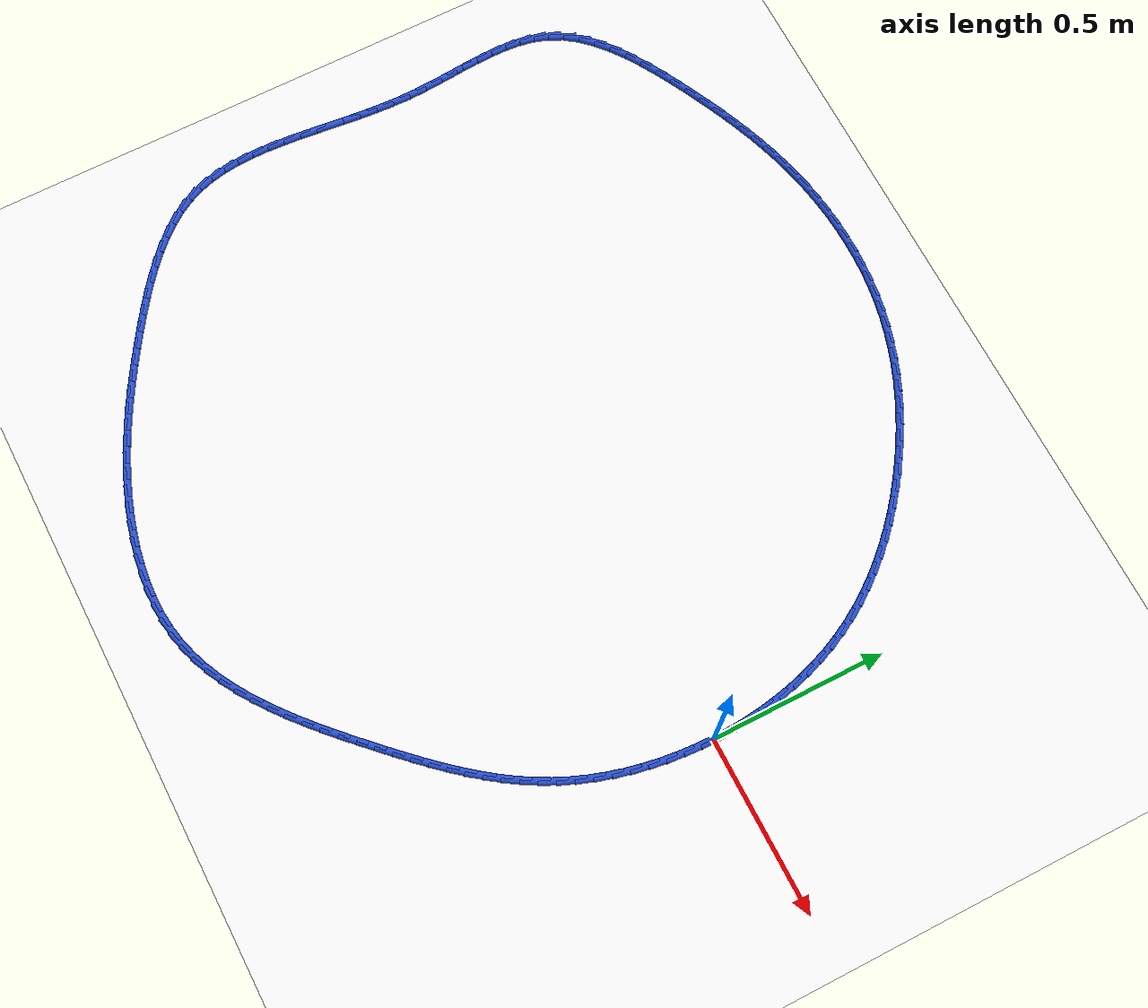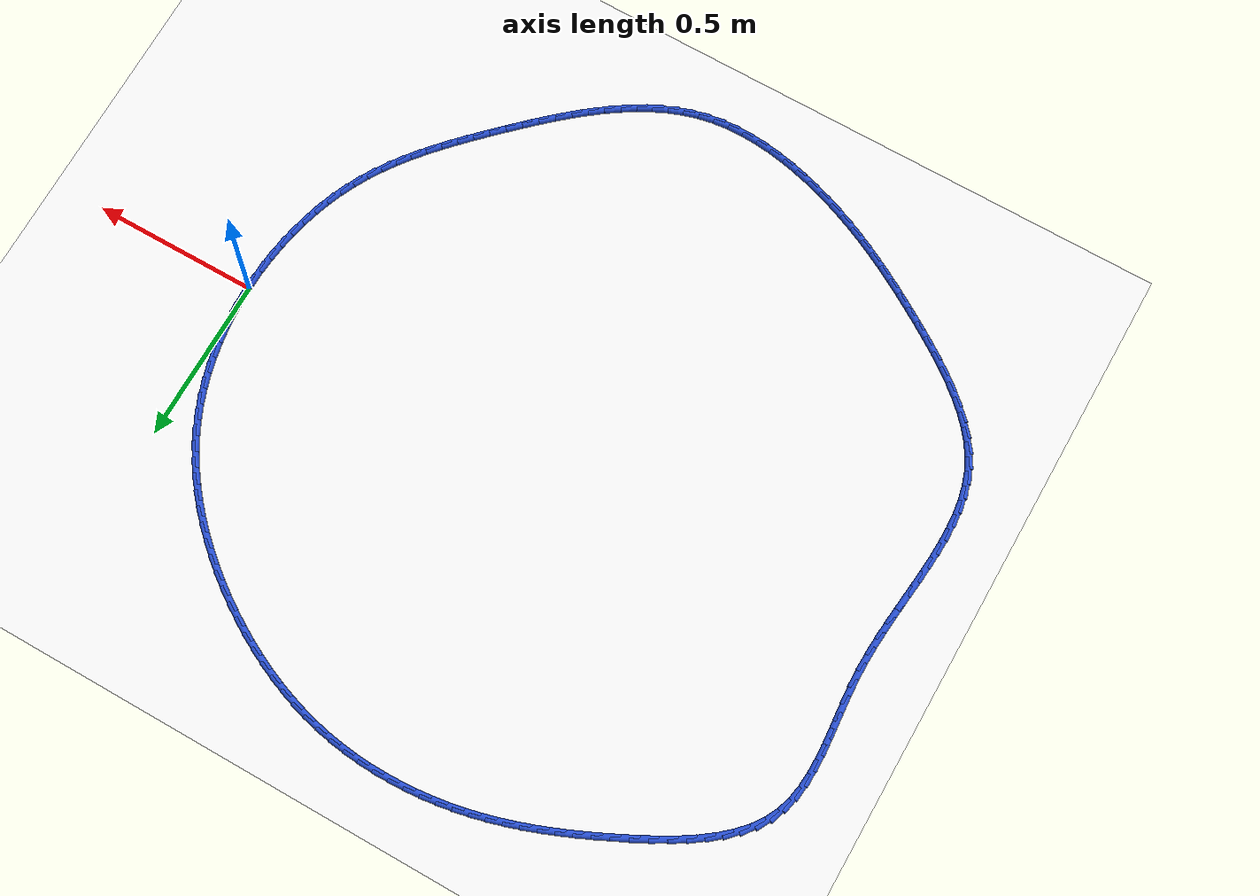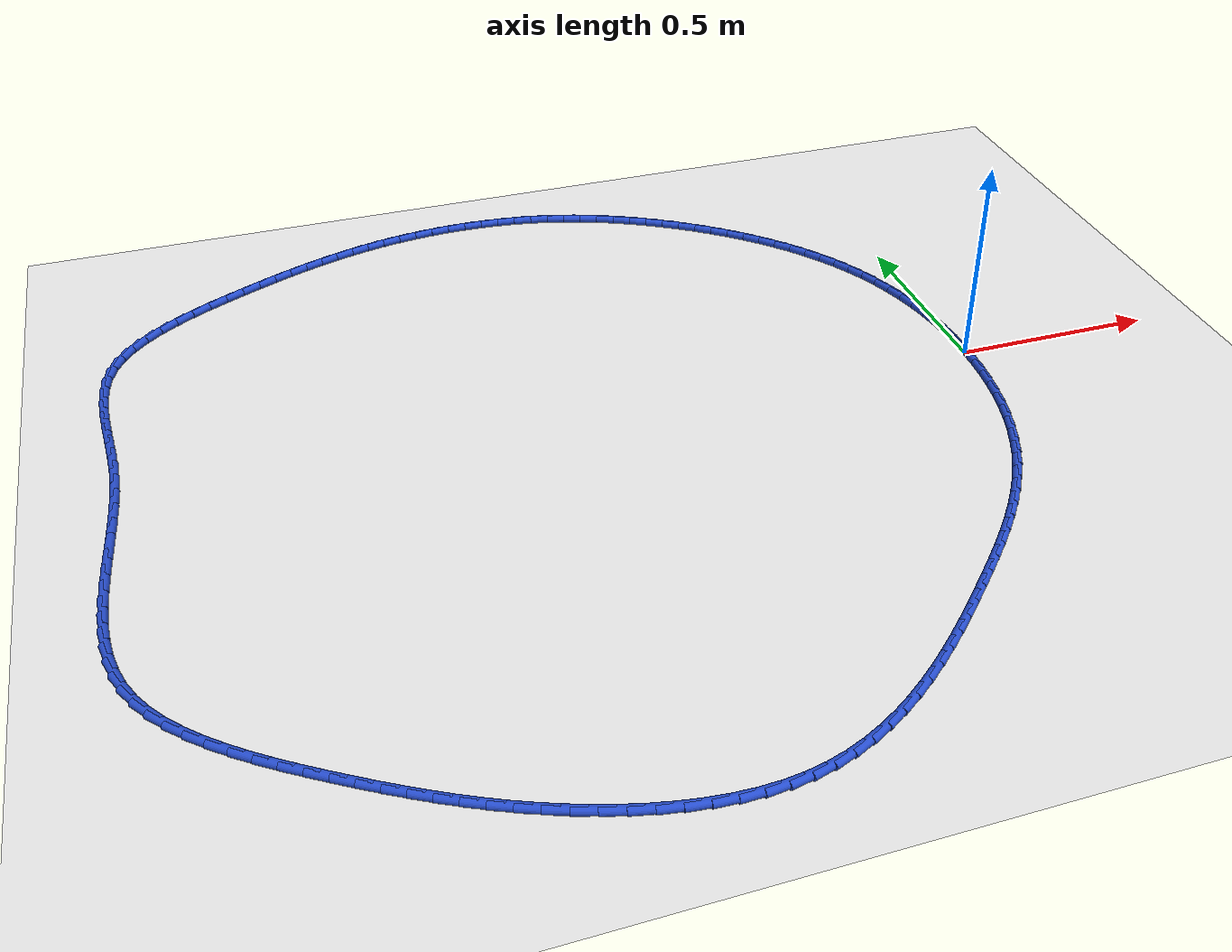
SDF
<sdf version="1.6">
 <world name="default">
  <light name="sun" type="directional">
   <pose>0 0 10 0 -0 0</pose>
   <diffuse>0.8 0.8 0.8 1</diffuse>
   <specular>0.2 0.2 0.2 1</specular>
   <attenuation>
    <range>1000</range>
    <constant>0.9</constant>
    <linear>0.01</linear>
    <quadratic>0.001</quadratic>
   </attenuation>
   <direction>-0.5 0.1 -0.9</direction>
  </light>
  <model name="ground_plane">
   <static>1</static>
   <link name="link">
    <collision name="collision">
     <geometry><plane><normal>0 0 1</normal><size>100 100</size></plane></geometry>
     <surface><friction><ode><mu>100</mu><mu2>50</mu2></ode></friction></surface>
    </collision>
    <visual name="visual">
     <cast_shadows>0</cast_shadows>
     <geometry><plane><normal>0 0 1</normal><size>100 100</size></plane></geometry>
     <material>
      <script><uri>file://media/materials/scripts/gazebo.material</uri><name>Gazebo/WhiteGlow</name></script>
     </material>
    </visual>
   </link>
  </model>
  <gravity>0 0 -9.8</gravity>
  <magnetic_field>6e-06 2.3e-05 -4.2e-05</magnetic_field>
  <atmosphere type="adiabatic"/>
  <physics name="default_physics" default="0" type="ode">
   <max_step_size>0.001</max_step_size>
   <real_time_factor>1</real_time_factor>
   <real_time_update_rate>1000</real_time_update_rate>
  </physics>
  <scene><ambient>0.4 0.4 0.4 1</ambient><background>0.7 0.7 0.7 1</background><shadows>1</shadows></scene>
  <spherical_coordinates>
   <surface_model>EARTH_WGS84</surface_model>
   <latitude_deg>0</latitude_deg>
   <longitude_deg>0</longitude_deg>
   <elevation>0</elevation>
   <heading_deg>0</heading_deg>
  </spherical_coordinates>
  <model name="line">
   <link name="link_0">
    <pose>-2.0816681711721685e-17 1.3877787807814457e-17 0.01 0 1.57 -1.5501064829622118</pose>
    <collision name="collision">
     <geometry><cylinder><radius>0.01</radius><length>0.08</length></cylinder></geometry>
    </collision>
    <visual name="visual">
     <material>
      <script><name>Gazebo/Blue</name><uri>file://media/materials/scripts/gazebo.material</uri></script>
     </material>
     <geometry><cylinder><radius>0.01</radius><length>0.08</length></cylinder></geometry>
    </visual>
   </link>
   <link name="link_1">
    <pose>-0.0009968287772393065 0.04817274329676447 0.01 0 1.57 -1.5047592067060662</pose>
    <collision name="collision">
     <geometry><cylinder><radius>0.01</radius><length>0.08</length></cylinder></geometry>
    </collision>
    <visual name="visual">
     <material>
      <script><name>Gazebo/Blue</name><uri>file://media/materials/scripts/gazebo.material</uri></script>
     </material>
     <geometry><cylinder><radius>0.01</radius><length>0.08</length></cylinder></geometry>
    </visual>
   </link>
   <link name="link_2">
    <pose>-0.0041706625471364615 0.09616421887775457 0.01 0 1.57 -1.4583500174845176</pose>
    <collision name="collision">
     <geometry><cylinder><radius>0.01</radius><length>0.08</length></cylinder></geometry>
    </collision>
    <visual name="visual">
     <material>
      <script><name>Gazebo/Blue</name><uri>file://media/materials/scripts/gazebo.material</uri></script>
     </material>
     <geometry><cylinder><radius>0.01</radius><length>0.08</length></cylinder></geometry>
    </visual>
   </link>
   <link name="link_3">
    <pose>-0.009554791758662765 0.14384401800369362 0.01 0 1.57 -1.4107031057219606</pose>
    <collision name="collision">
     <geometry><cylinder><radius>0.01</radius><length>0.08</length></cylinder></geometry>
    </collision>
    <visual name="visual">
     <material>
      <script><name>Gazebo/Blue</name><uri>file://media/materials/scripts/gazebo.material</uri></script>
     </material>
     <geometry><cylinder><radius>0.01</radius><length>0.08</length></cylinder></geometry>
    </visual>
   </link>
   <link name="link_4">
    <pose>-0.017182506860789485 0.19108173193530475 0.01 0 1.57 -1.3616522260447377</pose>
    <collision name="collision">
     <geometry><cylinder><radius>0.01</radius><length>0.08</length></cylinder></geometry>
    </collision>
    <visual name="visual">
     <material>
      <script><name>Gazebo/Blue</name><uri>file://media/materials/scripts/gazebo.material</uri></script>
     </material>
     <geometry><cylinder><radius>0.01</radius><length>0.08</length></cylinder></geometry>
    </visual>
   </link>
   <link name="link_5">
    <pose>-0.027087098302487927 0.23774695193331136 0.01 0 1.57 -1.3110444036572337</pose>
    <collision name="collision">
     <geometry><cylinder><radius>0.01</radius><length>0.08</length></cylinder></geometry>
    </collision>
    <visual name="visual">
     <material>
      <script><name>Gazebo/Blue</name><uri>file://media/materials/scripts/gazebo.material</uri></script>
     </material>
     <geometry><cylinder><radius>0.01</radius><length>0.08</length></cylinder></geometry>
    </visual>
   </link>
   <link name="link_6">
    <pose>-0.03930185653272936 0.28370926925843665 0.01 0 1.57 -1.2587447396442484</pose>
    <collision name="collision">
     <geometry><cylinder><radius>0.01</radius><length>0.08</length></cylinder></geometry>
    </collision>
    <visual name="visual">
     <material>
      <script><name>Gazebo/Blue</name><uri>file://media/materials/scripts/gazebo.material</uri></script>
     </material>
     <geometry><cylinder><radius>0.01</radius><length>0.08</length></cylinder></geometry>
    </visual>
   </link>
   <link name="link_7">
    <pose>-0.05386007200048504 0.3288382751714037 0.01 0 1.57 -1.204642352678541</pose>
    <collision name="collision">
     <geometry><cylinder><radius>0.01</radius><length>0.08</length></cylinder></geometry>
    </collision>
    <visual name="visual">
     <material>
      <script><name>Gazebo/Blue</name><uri>file://media/materials/scripts/gazebo.material</uri></script>
     </material>
     <geometry><cylinder><radius>0.01</radius><length>0.08</length></cylinder></geometry>
    </visual>
   </link>
   <link name="link_8">
    <pose>-0.0707950351547263 0.37300356093293585 0.01 0 1.57 -1.1486573845259487</pose>
    <collision name="collision">
     <geometry><cylinder><radius>0.01</radius><length>0.08</length></cylinder></geometry>
    </collision>
    <visual name="visual">
     <material>
      <script><name>Gazebo/Blue</name><uri>file://media/materials/scripts/gazebo.material</uri></script>
     </material>
     <geometry><cylinder><radius>0.01</radius><length>0.08</length></cylinder></geometry>
    </visual>
   </link>
   <link name="link_9">
    <pose>-0.09014003644442435 0.4160747178037565 0.01 0 1.57 -1.0908922614907033</pose>
    <collision name="collision">
     <geometry><cylinder><radius>0.01</radius><length>0.08</length></cylinder></geometry>
    </collision>
    <visual name="visual">
     <material>
      <script><name>Gazebo/Blue</name><uri>file://media/materials/scripts/gazebo.material</uri></script>
     </material>
     <geometry><cylinder><radius>0.01</radius><length>0.08</length></cylinder></geometry>
    </visual>
   </link>
   <link name="link_10">
    <pose>-0.11192263425703565 0.4579249805710866 0.01 0 1.57 -1.03370390258395</pose>
    <collision name="collision">
     <geometry><cylinder><radius>0.01</radius><length>0.08</length></cylinder></geometry>
    </collision>
    <visual name="visual">
     <material>
      <script><name>Gazebo/Blue</name><uri>file://media/materials/scripts/gazebo.material</uri></script>
     </material>
     <geometry><cylinder><radius>0.01</radius><length>0.08</length></cylinder></geometry>
    </visual>
   </link>
   <link name="link_11">
    <pose>-0.13607674020549693 0.4984871096402028 0.01 0 1.57 -0.9790467698159384</pose>
    <collision name="collision">
     <geometry><cylinder><radius>0.01</radius><length>0.08</length></cylinder></geometry>
    </collision>
    <visual name="visual">
     <material>
      <script><name>Gazebo/Blue</name><uri>file://media/materials/scripts/gazebo.material</uri></script>
     </material>
     <geometry><cylinder><radius>0.01</radius><length>0.08</length></cylinder></geometry>
    </visual>
   </link>
   <link name="link_12">
    <pose>-0.16245992196865988 0.5377423926602141 0.01 0 1.57 -0.9269705932287826</pose>
    <collision name="collision">
     <geometry><cylinder><radius>0.01</radius><length>0.08</length></cylinder></geometry>
    </collision>
    <visual name="visual">
     <material>
      <script><name>Gazebo/Blue</name><uri>file://media/materials/scripts/gazebo.material</uri></script>
     </material>
     <geometry><cylinder><radius>0.01</radius><length>0.08</length></cylinder></geometry>
    </visual>
   </link>
   <link name="link_13">
    <pose>-0.19092752106498592 0.5756735323163991 0.01 0 1.57 -0.8774153725735977</pose>
    <collision name="collision">
     <geometry><cylinder><radius>0.01</radius><length>0.08</length></cylinder></geometry>
    </collision>
    <visual name="visual">
     <material>
      <script><name>Gazebo/Blue</name><uri>file://media/materials/scripts/gazebo.material</uri></script>
     </material>
     <geometry><cylinder><radius>0.01</radius><length>0.08</length></cylinder></geometry>
    </visual>
   </link>
   <link name="link_14">
    <pose>-0.22133487901293625 0.6122632312940358 0.01 0 1.57 -0.8302790102618446</pose>
    <collision name="collision">
     <geometry><cylinder><radius>0.01</radius><length>0.08</length></cylinder></geometry>
    </collision>
    <visual name="visual">
     <material>
      <script><name>Gazebo/Blue</name><uri>file://media/materials/scripts/gazebo.material</uri></script>
     </material>
     <geometry><cylinder><radius>0.01</radius><length>0.08</length></cylinder></geometry>
    </visual>
   </link>
   <link name="link_15">
    <pose>-0.25353733733097245 0.6474941922784037 0.01 0 1.57 -0.7854280782524387</pose>
    <collision name="collision">
     <geometry><cylinder><radius>0.01</radius><length>0.08</length></cylinder></geometry>
    </collision>
    <visual name="visual">
     <material>
      <script><name>Gazebo/Blue</name><uri>file://media/materials/scripts/gazebo.material</uri></script>
     </material>
     <geometry><cylinder><radius>0.01</radius><length>0.08</length></cylinder></geometry>
    </visual>
   </link>
   <link name="link_16">
    <pose>-0.28739023753755577 0.6813491179547806 0.01 0 1.57 -0.7427069437953605</pose>
    <collision name="collision">
     <geometry><cylinder><radius>0.01</radius><length>0.08</length></cylinder></geometry>
    </collision>
    <visual name="visual">
     <material>
      <script><name>Gazebo/Blue</name><uri>file://media/materials/scripts/gazebo.material</uri></script>
     </material>
     <geometry><cylinder><radius>0.01</radius><length>0.08</length></cylinder></geometry>
    </visual>
   </link>
   <link name="link_17">
    <pose>-0.32274892115114767 0.7138107110084456 0.01 0 1.57 -0.7019450890808764</pose>
    <collision name="collision">
     <geometry><cylinder><radius>0.01</radius><length>0.08</length></cylinder></geometry>
    </collision>
    <visual name="visual">
     <material>
      <script><name>Gazebo/Blue</name><uri>file://media/materials/scripts/gazebo.material</uri></script>
     </material>
     <geometry><cylinder><radius>0.01</radius><length>0.08</length></cylinder></geometry>
    </visual>
   </link>
   <link name="link_18">
    <pose>-0.3594687296902093 0.744861674124677 0.01 0 1.57 -0.6629626662306229</pose>
    <collision name="collision">
     <geometry><cylinder><radius>0.01</radius><length>0.08</length></cylinder></geometry>
    </collision>
    <visual name="visual">
     <material>
      <script><name>Gazebo/Blue</name><uri>file://media/materials/scripts/gazebo.material</uri></script>
     </material>
     <geometry><cylinder><radius>0.01</radius><length>0.08</length></cylinder></geometry>
    </visual>
   </link>
   <link name="link_19">
    <pose>-0.3974050046732024 0.7744847099887533 0.01 0 1.57 -0.6255744449188403</pose>
    <collision name="collision">
     <geometry><cylinder><radius>0.01</radius><length>0.08</length></cylinder></geometry>
    </collision>
    <visual name="visual">
     <material>
      <script><name>Gazebo/Blue</name><uri>file://media/materials/scripts/gazebo.material</uri></script>
     </material>
     <geometry><cylinder><radius>0.01</radius><length>0.08</length></cylinder></geometry>
    </visual>
   </link>
   <link name="link_20">
    <pose>-0.4364130876185881 0.8026625212859532 0.01 0 1.57 -0.589515610624368</pose>
    <collision name="collision">
     <geometry><cylinder><radius>0.01</radius><length>0.08</length></cylinder></geometry>
    </collision>
    <visual name="visual">
     <material>
      <script><name>Gazebo/Blue</name><uri>file://media/materials/scripts/gazebo.material</uri></script>
     </material>
     <geometry><cylinder><radius>0.01</radius><length>0.08</length></cylinder></geometry>
    </visual>
   </link>
   <link name="link_21">
    <pose>-0.4763516994914862 0.8293756347567736 0.01 0 1.57 -0.553298459223235</pose>
    <collision name="collision">
     <geometry><cylinder><radius>0.01</radius><length>0.08</length></cylinder></geometry>
    </collision>
    <visual name="visual">
     <material>
      <script><name>Gazebo/Blue</name><uri>file://media/materials/scripts/gazebo.material</uri></script>
     </material>
     <geometry><cylinder><radius>0.01</radius><length>0.08</length></cylinder></geometry>
    </visual>
   </link>
   <link name="link_22">
    <pose>-0.5171376382166036 0.8545671827781015 0.01 0 1.57 -0.5157108555644453</pose>
    <collision name="collision">
     <geometry><cylinder><radius>0.01</radius><length>0.08</length></cylinder></geometry>
    </collision>
    <visual name="visual">
     <material>
      <script><name>Gazebo/Blue</name><uri>file://media/materials/scripts/gazebo.material</uri></script>
     </material>
     <geometry><cylinder><radius>0.01</radius><length>0.08</length></cylinder></geometry>
    </visual>
   </link>
   <link name="link_23">
    <pose>-0.5587365917634796 0.8781488185976425 0.01 0 1.57 -0.4766401149393161</pose>
    <collision name="collision">
     <geometry><cylinder><radius>0.01</radius><length>0.08</length></cylinder></geometry>
    </collision>
    <visual name="visual">
     <material>
      <script><name>Gazebo/Blue</name><uri>file://media/materials/scripts/gazebo.material</uri></script>
     </material>
     <geometry><cylinder><radius>0.01</radius><length>0.08</length></cylinder></geometry>
    </visual>
   </link>
   <link name="link_24">
    <pose>-0.601115773070034 0.9000312135724758 0.01 0 1.57 -0.4360189851619005</pose>
    <collision name="collision">
     <geometry><cylinder><radius>0.01</radius><length>0.08</length></cylinder></geometry>
    </collision>
    <visual name="visual">
     <material>
      <script><name>Gazebo/Blue</name><uri>file://media/materials/scripts/gazebo.material</uri></script>
     </material>
     <geometry><cylinder><radius>0.01</radius><length>0.08</length></cylinder></geometry>
    </visual>
   </link>
   <link name="link_25">
    <pose>-0.644242395074187 0.9201250390596825 0.01 0 1.57 -0.39379423912293726</pose>
    <collision name="collision">
     <geometry><cylinder><radius>0.01</radius><length>0.08</length></cylinder></geometry>
    </collision>
    <visual name="visual">
     <material>
      <script><name>Gazebo/Blue</name><uri>file://media/materials/scripts/gazebo.material</uri></script>
     </material>
     <geometry><cylinder><radius>0.01</radius><length>0.08</length></cylinder></geometry>
    </visual>
   </link>
   <link name="link_26">
    <pose>-0.688083670713859 0.9383409664163425 0.01 0 1.57 -0.3499303330273938</pose>
    <collision name="collision">
     <geometry><cylinder><radius>0.01</radius><length>0.08</length></cylinder></geometry>
    </collision>
    <visual name="visual">
     <material>
      <script><name>Gazebo/Blue</name><uri>file://media/materials/scripts/gazebo.material</uri></script>
     </material>
     <geometry><cylinder><radius>0.01</radius><length>0.08</length></cylinder></geometry>
    </visual>
   </link>
   <link name="link_27">
    <pose>-0.7326068129269697 0.9545896669995354 0.01 0 1.57 -0.3044133907731352</pose>
    <collision name="collision">
     <geometry><cylinder><radius>0.01</radius><length>0.08</length></cylinder></geometry>
    </collision>
    <visual name="visual">
     <material>
      <script><name>Gazebo/Blue</name><uri>file://media/materials/scripts/gazebo.material</uri></script>
     </material>
     <geometry><cylinder><radius>0.01</radius><length>0.08</length></cylinder></geometry>
    </visual>
   </link>
   <link name="link_28">
    <pose>-0.7777790346514398 0.9687818121663424 0.01 0 1.57 -0.25725533297576175</pose>
    <collision name="collision">
     <geometry><cylinder><radius>0.01</radius><length>0.08</length></cylinder></geometry>
    </collision>
    <visual name="visual">
     <material>
      <script><name>Gazebo/Blue</name><uri>file://media/materials/scripts/gazebo.material</uri></script>
     </material>
     <geometry><cylinder><radius>0.01</radius><length>0.08</length></cylinder></geometry>
    </visual>
   </link>
   <link name="link_29">
    <pose>-0.8235675488251893 0.980828073273843 0.01 0 1.57 -0.20849788737399966</pose>
    <collision name="collision">
     <geometry><cylinder><radius>0.01</radius><length>0.08</length></cylinder></geometry>
    </collision>
    <visual name="visual">
     <material>
      <script><name>Gazebo/Blue</name><uri>file://media/materials/scripts/gazebo.material</uri></script>
     </material>
     <geometry><cylinder><radius>0.01</radius><length>0.08</length></cylinder></geometry>
    </visual>
   </link>
   <link name="link_30">
    <pose>-0.8699395683861386 0.9906391216791179 0.01 0 1.57 -0.15850665656333882</pose>
    <collision name="collision">
     <geometry><cylinder><radius>0.01</radius><length>0.08</length></cylinder></geometry>
    </collision>
    <visual name="visual">
     <material>
      <script><name>Gazebo/Blue</name><uri>file://media/materials/scripts/gazebo.material</uri></script>
     </material>
     <geometry><cylinder><radius>0.01</radius><length>0.08</length></cylinder></geometry>
    </visual>
   </link>
   <link name="link_31">
    <pose>-0.9168522140037848 0.9981379951949938 0.01 0 1.57 -0.10958537922510585</pose>
    <collision name="collision">
     <geometry><cylinder><radius>0.01</radius><length>0.08</length></cylinder></geometry>
    </collision>
    <visual name="visual">
     <material>
      <script><name>Gazebo/Blue</name><uri>file://media/materials/scripts/gazebo.material</uri></script>
     </material>
     <geometry><cylinder><radius>0.01</radius><length>0.08</length></cylinder></geometry>
    </visual>
   </link>
   <link name="link_32">
    <pose>-0.96418274266268 1.0033455917668581 0.01 0 1.57 -0.06261789756660427</pose>
    <collision name="collision">
     <geometry><cylinder><radius>0.01</radius><length>0.08</length></cylinder></geometry>
    </collision>
    <visual name="visual">
     <material>
      <script><name>Gazebo/Blue</name><uri>file://media/materials/scripts/gazebo.material</uri></script>
     </material>
     <geometry><cylinder><radius>0.01</radius><length>0.08</length></cylinder></geometry>
    </visual>
   </link>
   <link name="link_33">
    <pose>-1.011770442358572 1.0063293342441297 0.01 0 1.57 -0.017354089174362174</pose>
    <collision name="collision">
     <geometry><cylinder><radius>0.01</radius><length>0.08</length></cylinder></geometry>
    </collision>
    <visual name="visual">
     <material>
      <script><name>Gazebo/Blue</name><uri>file://media/materials/scripts/gazebo.material</uri></script>
     </material>
     <geometry><cylinder><radius>0.01</radius><length>0.08</length></cylinder></geometry>
    </visual>
   </link>
   <link name="link_34">
    <pose>-1.0594543701429253 1.007156928461393 0.01 0 1.57 0.02647153548212108</pose>
    <collision name="collision">
     <geometry><cylinder><radius>0.01</radius><length>0.08</length></cylinder></geometry>
    </collision>
    <visual name="visual">
     <material>
      <script><name>Gazebo/Blue</name><uri>file://media/materials/scripts/gazebo.material</uri></script>
     </material>
     <geometry><cylinder><radius>0.01</radius><length>0.08</length></cylinder></geometry>
    </visual>
   </link>
   <link name="link_35">
    <pose>-1.1070735830672032 1.0058960802532328 0.01 0 1.57 0.06913082343619277</pose>
    <collision name="collision">
     <geometry><cylinder><radius>0.01</radius><length>0.08</length></cylinder></geometry>
    </collision>
    <visual name="visual">
     <material>
      <script><name>Gazebo/Blue</name><uri>file://media/materials/scripts/gazebo.material</uri></script>
     </material>
     <geometry><cylinder><radius>0.01</radius><length>0.08</length></cylinder></geometry>
    </visual>
   </link>
   <link name="link_36">
    <pose>-1.1544671381828704 1.002614495454234 0.01 0 1.57 0.11090141057207606</pose>
    <collision name="collision">
     <geometry><cylinder><radius>0.01</radius><length>0.08</length></cylinder></geometry>
    </collision>
    <visual name="visual">
     <material>
      <script><name>Gazebo/Blue</name><uri>file://media/materials/scripts/gazebo.material</uri></script>
     </material>
     <geometry><cylinder><radius>0.01</radius><length>0.08</length></cylinder></geometry>
    </visual>
   </link>
   <link name="link_37">
    <pose>-1.2014740925413911 0.9973798798989809 0.01 0 1.57 0.15206765910142425</pose>
    <collision name="collision">
     <geometry><cylinder><radius>0.01</radius><length>0.08</length></cylinder></geometry>
    </collision>
    <visual name="visual">
     <material>
      <script><name>Gazebo/Blue</name><uri>file://media/materials/scripts/gazebo.material</uri></script>
     </material>
     <geometry><cylinder><radius>0.01</radius><length>0.08</length></cylinder></geometry>
    </visual>
   </link>
   <link name="link_38">
    <pose>-1.247933503194229 0.9902599394220583 0.01 0 1.57 0.19281319013708983</pose>
    <collision name="collision">
     <geometry><cylinder><radius>0.01</radius><length>0.08</length></cylinder></geometry>
    </collision>
    <visual name="visual">
     <material>
      <script><name>Gazebo/Blue</name><uri>file://media/materials/scripts/gazebo.material</uri></script>
     </material>
     <geometry><cylinder><radius>0.01</radius><length>0.08</length></cylinder></geometry>
    </visual>
   </link>
   <link name="link_39">
    <pose>-1.2937083928378108 0.9813229110403985 0.01 0 1.57 0.23237854974749306</pose>
    <collision name="collision">
     <geometry><cylinder><radius>0.01</radius><length>0.08</length></cylinder></geometry>
    </collision>
    <visual name="visual">
     <material>
      <script><name>Gazebo/Blue</name><uri>file://media/materials/scripts/gazebo.material</uri></script>
     </material>
     <geometry><cylinder><radius>0.01</radius><length>0.08</length></cylinder></geometry>
    </visual>
   </link>
   <link name="link_40">
    <pose>-1.3388452807901616 0.970641098849715 0.01 0 1.57 0.2700132768177109</pose>
    <collision name="collision">
     <geometry><cylinder><radius>0.01</radius><length>0.08</length></cylinder></geometry>
    </collision>
    <visual name="visual">
     <material>
      <script><name>Gazebo/Blue</name><uri>file://media/materials/scripts/gazebo.material</uri></script>
     </material>
     <geometry><cylinder><radius>0.01</radius><length>0.08</length></cylinder></geometry>
    </visual>
   </link>
   <link name="link_41">
    <pose>-1.3834754928381867 0.9582886866238713 0.01 0 1.57 0.3053333354892284</pose>
    <collision name="collision">
     <geometry><cylinder><radius>0.01</radius><length>0.08</length></cylinder></geometry>
    </collision>
    <visual name="visual">
     <material>
      <script><name>Gazebo/Blue</name><uri>file://media/materials/scripts/gazebo.material</uri></script>
     </material>
     <geometry><cylinder><radius>0.01</radius><length>0.08</length></cylinder></geometry>
    </visual>
   </link>
   <link name="link_42">
    <pose>-1.427730812893504 0.9443398682907568 0.01 0 1.57 0.3380254209365037</pose>
    <collision name="collision">
     <geometry><cylinder><radius>0.01</radius><length>0.08</length></cylinder></geometry>
    </collision>
    <visual name="visual">
     <material>
      <script><name>Gazebo/Blue</name><uri>file://media/materials/scripts/gazebo.material</uri></script>
     </material>
     <geometry><cylinder><radius>0.01</radius><length>0.08</length></cylinder></geometry>
    </visual>
   </link>
   <link name="link_43">
    <pose>-1.4717430248677315 0.9288688377782597 0.01 0 1.57 0.3678501503930944</pose>
    <collision name="collision">
     <geometry><cylinder><radius>0.01</radius><length>0.08</length></cylinder></geometry>
    </collision>
    <visual name="visual">
     <material>
      <script><name>Gazebo/Blue</name><uri>file://media/materials/scripts/gazebo.material</uri></script>
     </material>
     <geometry><cylinder><radius>0.01</radius><length>0.08</length></cylinder></geometry>
    </visual>
   </link>
   <link name="link_44">
    <pose>-1.5156439126724897 0.911949789014269 0.01 0 1.57 0.394641956208301</pose>
    <collision name="collision">
     <geometry><cylinder><radius>0.01</radius><length>0.08</length></cylinder></geometry>
    </collision>
    <visual name="visual">
     <material>
      <script><name>Gazebo/Blue</name><uri>file://media/materials/scripts/gazebo.material</uri></script>
     </material>
     <geometry><cylinder><radius>0.01</radius><length>0.08</length></cylinder></geometry>
    </visual>
   </link>
   <link name="link_45">
    <pose>-1.5595652602193946 0.8936569159266732 0.01 0 1.57 0.41830467473521493</pose>
    <collision name="collision">
     <geometry><cylinder><radius>0.01</radius><length>0.08</length></cylinder></geometry>
    </collision>
    <visual name="visual">
     <material>
      <script><name>Gazebo/Blue</name><uri>file://media/materials/scripts/gazebo.material</uri></script>
     </material>
     <geometry><cylinder><radius>0.01</radius><length>0.08</length></cylinder></geometry>
    </visual>
   </link>
   <link name="link_46">
    <pose>-1.603638851420067 0.8740644124433615 0.01 0 1.57 0.43880418753843414</pose>
    <collision name="collision">
     <geometry><cylinder><radius>0.01</radius><length>0.08</length></cylinder></geometry>
    </collision>
    <visual name="visual">
     <material>
      <script><name>Gazebo/Blue</name><uri>file://media/materials/scripts/gazebo.material</uri></script>
     </material>
     <geometry><cylinder><radius>0.01</radius><length>0.08</length></cylinder></geometry>
    </visual>
   </link>
   <link name="link_47">
    <pose>-1.6479964701861238 0.8532464724922223 0.01 0 1.57 0.45616170460569394</pose>
    <collision name="collision">
     <geometry><cylinder><radius>0.01</radius><length>0.08</length></cylinder></geometry>
    </collision>
    <visual name="visual">
     <material>
      <script><name>Gazebo/Blue</name><uri>file://media/materials/scripts/gazebo.material</uri></script>
     </material>
     <geometry><cylinder><radius>0.01</radius><length>0.08</length></cylinder></geometry>
    </visual>
   </link>
   <link name="link_48">
    <pose>-1.692769735733515 0.831277245666697 0.01 0 1.57 0.473330192097099</pose>
    <collision name="collision">
     <geometry><cylinder><radius>0.01</radius><length>0.08</length></cylinder></geometry>
    </collision>
    <visual name="visual">
     <material>
      <script><name>Gazebo/Blue</name><uri>file://media/materials/scripts/gazebo.material</uri></script>
     </material>
     <geometry><cylinder><radius>0.01</radius><length>0.08</length></cylinder></geometry>
    </visual>
   </link>
   <link name="link_49">
    <pose>-1.7378789513808093 0.8081739974080445 0.01 0 1.57 0.4990859575301556</pose>
    <collision name="collision">
     <geometry><cylinder><radius>0.01</radius><length>0.08</length></cylinder></geometry>
    </collision>
    <visual name="visual">
     <material>
      <script><name>Gazebo/Blue</name><uri>file://media/materials/scripts/gazebo.material</uri></script>
     </material>
     <geometry><cylinder><radius>0.01</radius><length>0.08</length></cylinder></geometry>
    </visual>
   </link>
   <link name="link_50">
    <pose>-1.7826187959940611 0.7837855812348622 0.01 0 1.57 0.5357770178642751</pose>
    <collision name="collision">
     <geometry><cylinder><radius>0.01</radius><length>0.08</length></cylinder></geometry>
    </collision>
    <visual name="visual">
     <material>
      <script><name>Gazebo/Blue</name><uri>file://media/materials/scripts/gazebo.material</uri></script>
     </material>
     <geometry><cylinder><radius>0.01</radius><length>0.08</length></cylinder></geometry>
    </visual>
   </link>
   <link name="link_51">
    <pose>-1.826168716723446 0.7579298314261004 0.01 0 1.57 0.5848675909256249</pose>
    <collision name="collision">
     <geometry><cylinder><radius>0.01</radius><length>0.08</length></cylinder></geometry>
    </collision>
    <visual name="visual">
     <material>
      <script><name>Gazebo/Blue</name><uri>file://media/materials/scripts/gazebo.material</uri></script>
     </material>
     <geometry><cylinder><radius>0.01</radius><length>0.08</length></cylinder></geometry>
    </visual>
   </link>
   <link name="link_52">
    <pose>-1.8677081607191417 0.7304245822607092 0.01 0 1.57 0.6485347987169418</pose>
    <collision name="collision">
     <geometry><cylinder><radius>0.01</radius><length>0.08</length></cylinder></geometry>
    </collision>
    <visual name="visual">
     <material>
      <script><name>Gazebo/Blue</name><uri>file://media/materials/scripts/gazebo.material</uri></script>
     </material>
     <geometry><cylinder><radius>0.01</radius><length>0.08</length></cylinder></geometry>
    </visual>
   </link>
   <link name="link_53">
    <pose>-1.9064165751313236 0.7010876680176386 0.01 0 1.57 0.7296478006516522</pose>
    <collision name="collision">
     <geometry><cylinder><radius>0.01</radius><length>0.08</length></cylinder></geometry>
    </collision>
    <visual name="visual">
     <material>
      <script><name>Gazebo/Blue</name><uri>file://media/materials/scripts/gazebo.material</uri></script>
     </material>
     <geometry><cylinder><radius>0.01</radius><length>0.08</length></cylinder></geometry>
    </visual>
   </link>
   <link name="link_54">
    <pose>-1.9414734071101702 0.669736922975839 0.01 0 1.57 0.8315524580705179</pose>
    <collision name="collision">
     <geometry><cylinder><radius>0.01</radius><length>0.08</length></cylinder></geometry>
    </collision>
    <visual name="visual">
     <material>
      <script><name>Gazebo/Blue</name><uri>file://media/materials/scripts/gazebo.material</uri></script>
     </material>
     <geometry><cylinder><radius>0.01</radius><length>0.08</length></cylinder></geometry>
    </visual>
   </link>
   <link name="link_55">
    <pose>-1.9720581038058582 0.6361901814142601 0.01 0 1.57 0.9573745315002794</pose>
    <collision name="collision">
     <geometry><cylinder><radius>0.01</radius><length>0.08</length></cylinder></geometry>
    </collision>
    <visual name="visual">
     <material>
      <script><name>Gazebo/Blue</name><uri>file://media/materials/scripts/gazebo.material</uri></script>
     </material>
     <geometry><cylinder><radius>0.01</radius><length>0.08</length></cylinder></geometry>
    </visual>
   </link>
   <link name="link_56">
    <pose>-1.9973501123685637 0.6002652776118523 0.01 0 1.57 1.1080111142095896</pose>
    <collision name="collision">
     <geometry><cylinder><radius>0.01</radius><length>0.08</length></cylinder></geometry>
    </collision>
    <visual name="visual">
     <material>
      <script><name>Gazebo/Blue</name><uri>file://media/materials/scripts/gazebo.material</uri></script>
     </material>
     <geometry><cylinder><radius>0.01</radius><length>0.08</length></cylinder></geometry>
    </visual>
   </link>
   <link name="link_57">
    <pose>-2.016548685299851 0.5617852047945094 0.01 0 1.57 1.2628221735462937</pose>
    <collision name="collision">
     <geometry><cylinder><radius>0.01</radius><length>0.08</length></cylinder></geometry>
    </collision>
    <visual name="visual">
     <material>
      <script><name>Gazebo/Blue</name><uri>file://media/materials/scripts/gazebo.material</uri></script>
     </material>
     <geometry><cylinder><radius>0.01</radius><length>0.08</length></cylinder></geometry>
    </visual>
   </link>
   <link name="link_58">
    <pose>-2.0295965057450793 0.5207666068420831 0.01 0 1.57 1.3927543149951749</pose>
    <collision name="collision">
     <geometry><cylinder><radius>0.01</radius><length>0.08</length></cylinder></geometry>
    </collision>
    <visual name="visual">
     <material>
      <script><name>Gazebo/Blue</name><uri>file://media/materials/scripts/gazebo.material</uri></script>
     </material>
     <geometry><cylinder><radius>0.01</radius><length>0.08</length></cylinder></geometry>
    </visual>
   </link>
   <link name="link_59">
    <pose>-2.0373869412470103 0.47747376425903615 0.01 0 1.57 1.493917456766035</pose>
    <collision name="collision">
     <geometry><cylinder><radius>0.01</radius><length>0.08</length></cylinder></geometry>
    </collision>
    <visual name="visual">
     <material>
      <script><name>Gazebo/Blue</name><uri>file://media/materials/scripts/gazebo.material</uri></script>
     </material>
     <geometry><cylinder><radius>0.01</radius><length>0.08</length></cylinder></geometry>
    </visual>
   </link>
   <link name="link_60">
    <pose>-2.0408754027772877 0.4321871187757354 0.01 0 1.57 1.567777218730004</pose>
    <collision name="collision">
     <geometry><cylinder><radius>0.01</radius><length>0.08</length></cylinder></geometry>
    </collision>
    <visual name="visual">
     <material>
      <script><name>Gazebo/Blue</name><uri>file://media/materials/scripts/gazebo.material</uri></script>
     </material>
     <geometry><cylinder><radius>0.01</radius><length>0.08</length></cylinder></geometry>
    </visual>
   </link>
   <link name="link_61">
    <pose>-2.0410173013075603 0.3851871121225471 0.01 0 1.57 -1.5243890836388692</pose>
    <collision name="collision">
     <geometry><cylinder><radius>0.01</radius><length>0.08</length></cylinder></geometry>
    </collision>
    <visual name="visual">
     <material>
      <script><name>Gazebo/Blue</name><uri>file://media/materials/scripts/gazebo.material</uri></script>
     </material>
     <geometry><cylinder><radius>0.01</radius><length>0.08</length></cylinder></geometry>
    </visual>
   </link>
   <link name="link_62">
    <pose>-2.0387680478094747 0.3367541860298386 0.01 0 1.57 -1.4966165736617398</pose>
    <collision name="collision">
     <geometry><cylinder><radius>0.01</radius><length>0.08</length></cylinder></geometry>
    </collision>
    <visual name="visual">
     <material>
      <script><name>Gazebo/Blue</name><uri>file://media/materials/scripts/gazebo.material</uri></script>
     </material>
     <geometry><cylinder><radius>0.01</radius><length>0.08</length></cylinder></geometry>
    </visual>
   </link>
   <link name="link_63">
    <pose>-2.0350830532546786 0.2871687822279757 0.01 0 1.57 -1.488431836368806</pose>
    <collision name="collision">
     <geometry><cylinder><radius>0.01</radius><length>0.08</length></cylinder></geometry>
    </collision>
    <visual name="visual">
     <material>
      <script><name>Gazebo/Blue</name><uri>file://media/materials/scripts/gazebo.material</uri></script>
     </material>
     <geometry><cylinder><radius>0.01</radius><length>0.08</length></cylinder></geometry>
    </visual>
   </link>
   <link name="link_64">
    <pose>-2.0309177286148183 0.23671134244732578 0.01 0 1.57 -1.4986336305554313</pose>
    <collision name="collision">
     <geometry><cylinder><radius>0.01</radius><length>0.08</length></cylinder></geometry>
    </collision>
    <visual name="visual">
     <material>
      <script><name>Gazebo/Blue</name><uri>file://media/materials/scripts/gazebo.material</uri></script>
     </material>
     <geometry><cylinder><radius>0.01</radius><length>0.08</length></cylinder></geometry>
    </visual>
   </link>
   <link name="link_65">
    <pose>-2.0272274848615406 0.18566230841825507 0.01 0 1.57 -1.526826560147353</pose>
    <collision name="collision">
     <geometry><cylinder><radius>0.01</radius><length>0.08</length></cylinder></geometry>
    </collision>
    <visual name="visual">
     <material>
      <script><name>Gazebo/Blue</name><uri>file://media/materials/scripts/gazebo.material</uri></script>
     </material>
     <geometry><cylinder><radius>0.01</radius><length>0.08</length></cylinder></geometry>
    </visual>
   </link>
   <link name="link_66">
    <pose>-2.0249677329664926 0.13430212187112983 0.01 0 1.57 -1.5702740989880162</pose>
    <collision name="collision">
     <geometry><cylinder><radius>0.01</radius><length>0.08</length></cylinder></geometry>
    </collision>
    <visual name="visual">
     <material>
      <script><name>Gazebo/Blue</name><uri>file://media/materials/scripts/gazebo.material</uri></script>
     </material>
     <geometry><cylinder><radius>0.01</radius><length>0.08</length></cylinder></geometry>
    </visual>
   </link>
   <link name="link_67">
    <pose>-2.0249408862893046 0.08289414551727994 0.01 0 1.57 1.5307612153690153</pose>
    <collision name="collision">
     <geometry><cylinder><radius>0.01</radius><length>0.08</length></cylinder></geometry>
    </collision>
    <visual name="visual">
     <material>
      <script><name>Gazebo/Blue</name><uri>file://media/materials/scripts/gazebo.material</uri></script>
     </material>
     <geometry><cylinder><radius>0.01</radius><length>0.08</length></cylinder></geometry>
    </visual>
   </link>
   <link name="link_68">
    <pose>-2.0269957396386817 0.031595290279857406 0.01 0 1.57 1.5000644835520844</pose>
    <collision name="collision">
     <geometry><cylinder><radius>0.01</radius><length>0.08</length></cylinder></geometry>
    </collision>
    <visual name="visual">
     <material>
      <script><name>Gazebo/Blue</name><uri>file://media/materials/scripts/gazebo.material</uri></script>
     </material>
     <geometry><cylinder><radius>0.01</radius><length>0.08</length></cylinder></geometry>
    </visual>
   </link>
   <link name="link_69">
    <pose>-2.0306143178010094 -0.01947847520532467 0.01 0 1.57 1.4791299205607695</pose>
    <collision name="collision">
     <geometry><cylinder><radius>0.01</radius><length>0.08</length></cylinder></geometry>
    </collision>
    <visual name="visual">
     <material>
      <script><name>Gazebo/Blue</name><uri>file://media/materials/scripts/gazebo.material</uri></script>
     </material>
     <geometry><cylinder><radius>0.01</radius><length>0.08</length></cylinder></geometry>
    </visual>
   </link>
   <link name="link_70">
    <pose>-2.035277880113161 -0.07021126774906124 0.01 0 1.57 1.4679342129158153</pose>
    <collision name="collision">
     <geometry><cylinder><radius>0.01</radius><length>0.08</length></cylinder></geometry>
    </collision>
    <visual name="visual">
     <material>
      <script><name>Gazebo/Blue</name><uri>file://media/materials/scripts/gazebo.material</uri></script>
     </material>
     <geometry><cylinder><radius>0.01</radius><length>0.08</length></cylinder></geometry>
    </visual>
   </link>
   <link name="link_71">
    <pose>-2.040467685912013 -0.12048720416214555 0.01 0 1.57 1.466608077840592</pose>
    <collision name="collision">
     <geometry><cylinder><radius>0.01</radius><length>0.08</length></cylinder></geometry>
    </collision>
    <visual name="visual">
     <material>
      <script><name>Gazebo/Blue</name><uri>file://media/materials/scripts/gazebo.material</uri></script>
     </material>
     <geometry><cylinder><radius>0.01</radius><length>0.08</length></cylinder></geometry>
    </visual>
   </link>
   <link name="link_72">
    <pose>-2.0456649945344427 -0.17019040125537221 0.01 0 1.57 1.4754803716861484</pose>
    <collision name="collision">
     <geometry><cylinder><radius>0.01</radius><length>0.08</length></cylinder></geometry>
    </collision>
    <visual name="visual">
     <material>
      <script><name>Gazebo/Blue</name><uri>file://media/materials/scripts/gazebo.material</uri></script>
     </material>
     <geometry><cylinder><radius>0.01</radius><length>0.08</length></cylinder></geometry>
    </visual>
   </link>
   <link name="link_73">
    <pose>-2.050351065317325 -0.21920497583953613 0.01 0 1.57 1.4951045164778929</pose>
    <collision name="collision">
     <geometry><cylinder><radius>0.01</radius><length>0.08</length></cylinder></geometry>
    </collision>
    <visual name="visual">
     <material>
      <script><name>Gazebo/Blue</name><uri>file://media/materials/scripts/gazebo.material</uri></script>
     </material>
     <geometry><cylinder><radius>0.01</radius><length>0.08</length></cylinder></geometry>
    </visual>
   </link>
   <link name="link_74">
    <pose>-2.0540071575975354 -0.26741504472542993 0.01 0 1.57 1.5262627248158491</pose>
    <collision name="collision">
     <geometry><cylinder><radius>0.01</radius><length>0.08</length></cylinder></geometry>
    </collision>
    <visual name="visual">
     <material>
      <script><name>Gazebo/Blue</name><uri>file://media/materials/scripts/gazebo.material</uri></script>
     </material>
     <geometry><cylinder><radius>0.01</radius><length>0.08</length></cylinder></geometry>
    </visual>
   </link>
   <link name="link_75">
    <pose>-2.0561145307119486 -0.31470472472384836 0.01 0 1.57 1.5699334006370116</pose>
    <collision name="collision">
     <geometry><cylinder><radius>0.01</radius><length>0.08</length></cylinder></geometry>
    </collision>
    <visual name="visual">
     <material>
      <script><name>Gazebo/Blue</name><uri>file://media/materials/scripts/gazebo.material</uri></script>
     </material>
     <geometry><cylinder><radius>0.01</radius><length>0.08</length></cylinder></geometry>
    </visual>
   </link>
   <link name="link_76">
    <pose>-2.0561544439974426 -0.36095813264558574 0.01 0 1.57 -1.514399068019422</pose>
    <collision name="collision">
     <geometry><cylinder><radius>0.01</radius><length>0.08</length></cylinder></geometry>
    </collision>
    <visual name="visual">
     <material>
      <script><name>Gazebo/Blue</name><uri>file://media/materials/scripts/gazebo.material</uri></script>
     </material>
     <geometry><cylinder><radius>0.01</radius><length>0.08</length></cylinder></geometry>
    </visual>
   </link>
   <link name="link_77">
    <pose>-2.053608156790892 -0.40605938530143604 0.01 0 1.57 -1.4425779014602589</pose>
    <collision name="collision">
     <geometry><cylinder><radius>0.01</radius><length>0.08</length></cylinder></geometry>
    </collision>
    <visual name="visual">
     <material>
      <script><name>Gazebo/Blue</name><uri>file://media/materials/scripts/gazebo.material</uri></script>
     </material>
     <geometry><cylinder><radius>0.01</radius><length>0.08</length></cylinder></geometry>
    </visual>
   </link>
   <link name="link_78">
    <pose>-2.0479569284291723 -0.44989259950219407 0.01 0 1.57 -1.3556830743003094</pose>
    <collision name="collision">
     <geometry><cylinder><radius>0.01</radius><length>0.08</length></cylinder></geometry>
    </collision>
    <visual name="visual">
     <material>
      <script><name>Gazebo/Blue</name><uri>file://media/materials/scripts/gazebo.material</uri></script>
     </material>
     <geometry><cylinder><radius>0.01</radius><length>0.08</length></cylinder></geometry>
    </visual>
   </link>
   <link name="link_79">
    <pose>-2.03868201824916 -0.49234189205865264 0.01 0 1.57 -1.2541643250261785</pose>
    <collision name="collision">
     <geometry><cylinder><radius>0.01</radius><length>0.08</length></cylinder></geometry>
    </collision>
    <visual name="visual">
     <material>
      <script><name>Gazebo/Blue</name><uri>file://media/materials/scripts/gazebo.material</uri></script>
     </material>
     <geometry><cylinder><radius>0.01</radius><length>0.08</length></cylinder></geometry>
    </visual>
   </link>
   <link name="link_80">
    <pose>-2.025264685587731 -0.5332913797816068 0.01 0 1.57 -1.1400347652744238</pose>
    <collision name="collision">
     <geometry><cylinder><radius>0.01</radius><length>0.08</length></cylinder></geometry>
    </collision>
    <visual name="visual">
     <material>
      <script><name>Gazebo/Blue</name><uri>file://media/materials/scripts/gazebo.material</uri></script>
     </material>
     <geometry><cylinder><radius>0.01</radius><length>0.08</length></cylinder></geometry>
    </visual>
   </link>
   <link name="link_81">
    <pose>-2.0071888839568413 -0.5726256708765035 0.01 0 1.57 -1.0243611437298699</pose>
    <collision name="collision">
     <geometry><cylinder><radius>0.01</radius><length>0.08</length></cylinder></geometry>
    </collision>
    <visual name="visual">
     <material>
      <script><name>Gazebo/Blue</name><uri>file://media/materials/scripts/gazebo.material</uri></script>
     </material>
     <geometry><cylinder><radius>0.01</radius><length>0.08</length></cylinder></geometry>
    </visual>
   </link>
   <link name="link_82">
    <pose>-1.9842800178895819 -0.610291651315112 0.01 0 1.57 -0.9238509206600711</pose>
    <collision name="collision">
     <geometry><cylinder><radius>0.01</radius><length>0.08</length></cylinder></geometry>
    </collision>
    <visual name="visual">
     <material>
      <script><name>Gazebo/Blue</name><uri>file://media/materials/scripts/gazebo.material</uri></script>
     </material>
     <geometry><cylinder><radius>0.01</radius><length>0.08</length></cylinder></geometry>
    </visual>
   </link>
   <link name="link_83">
    <pose>-1.9570351204867271 -0.6463587064158225 0.01 0 1.57 -0.8394397360357235</pose>
    <collision name="collision">
     <geometry><cylinder><radius>0.01</radius><length>0.08</length></cylinder></geometry>
    </collision>
    <visual name="visual">
     <material>
      <script><name>Gazebo/Blue</name><uri>file://media/materials/scripts/gazebo.material</uri></script>
     </material>
     <geometry><cylinder><radius>0.01</radius><length>0.08</length></cylinder></geometry>
    </visual>
   </link>
   <link name="link_84">
    <pose>-1.9260295874808315 -0.680910514175532 0.01 0 1.57 -0.7694952050078162</pose>
    <collision name="collision">
     <geometry><cylinder><radius>0.01</radius><length>0.08</length></cylinder></geometry>
    </collision>
    <visual name="visual">
     <material>
      <script><name>Gazebo/Blue</name><uri>file://media/materials/scripts/gazebo.material</uri></script>
     </material>
     <geometry><cylinder><radius>0.01</radius><length>0.08</length></cylinder></geometry>
    </visual>
   </link>
   <link name="link_85">
    <pose>-1.891838814604451 -0.7140307525911375 0.01 0 1.57 -0.7122018706423913</pose>
    <collision name="collision">
     <geometry><cylinder><radius>0.01</radius><length>0.08</length></cylinder></geometry>
    </collision>
    <visual name="visual">
     <material>
      <script><name>Gazebo/Blue</name><uri>file://media/materials/scripts/gazebo.material</uri></script>
     </material>
     <geometry><cylinder><radius>0.01</radius><length>0.08</length></cylinder></geometry>
    </visual>
   </link>
   <link name="link_86">
    <pose>-1.8550381975901409 -0.7458030996595356 0.01 0 1.57 -0.6658875256018496</pose>
    <collision name="collision">
     <geometry><cylinder><radius>0.01</radius><length>0.08</length></cylinder></geometry>
    </collision>
    <visual name="visual">
     <material>
      <script><name>Gazebo/Blue</name><uri>file://media/materials/scripts/gazebo.material</uri></script>
     </material>
     <geometry><cylinder><radius>0.01</radius><length>0.08</length></cylinder></geometry>
    </visual>
   </link>
   <link name="link_87">
    <pose>-1.8162031321704577 -0.7763112333776243 0.01 0 1.57 -0.6291660363744604</pose>
    <collision name="collision">
     <geometry><cylinder><radius>0.01</radius><length>0.08</length></cylinder></geometry>
    </collision>
    <visual name="visual">
     <material>
      <script><name>Gazebo/Blue</name><uri>file://media/materials/scripts/gazebo.material</uri></script>
     </material>
     <geometry><cylinder><radius>0.01</radius><length>0.08</length></cylinder></geometry>
    </visual>
   </link>
   <link name="link_88">
    <pose>-1.7759090140779579 -0.805638831742299 0.01 0 1.57 -0.6009837653020444</pose>
    <collision name="collision">
     <geometry><cylinder><radius>0.01</radius><length>0.08</length></cylinder></geometry>
    </collision>
    <visual name="visual">
     <material>
      <script><name>Gazebo/Blue</name><uri>file://media/materials/scripts/gazebo.material</uri></script>
     </material>
     <geometry><cylinder><radius>0.01</radius><length>0.08</length></cylinder></geometry>
    </visual>
   </link>
   <link name="link_89">
    <pose>-1.7347312390451963 -0.8338695727504573 0.01 0 1.57 -0.5806274580564076</pose>
    <collision name="collision">
     <geometry><cylinder><radius>0.01</radius><length>0.08</length></cylinder></geometry>
    </collision>
    <visual name="visual">
     <material>
      <script><name>Gazebo/Blue</name><uri>file://media/materials/scripts/gazebo.material</uri></script>
     </material>
     <geometry><cylinder><radius>0.01</radius><length>0.08</length></cylinder></geometry>
    </visual>
   </link>
   <link name="link_90">
    <pose>-1.6932452028047285 -0.8610871343989953 0.01 0 1.57 -0.56701742146407</pose>
    <collision name="collision">
     <geometry><cylinder><radius>0.01</radius><length>0.08</length></cylinder></geometry>
    </collision>
    <visual name="visual">
     <material>
      <script><name>Gazebo/Blue</name><uri>file://media/materials/scripts/gazebo.material</uri></script>
     </material>
     <geometry><cylinder><radius>0.01</radius><length>0.08</length></cylinder></geometry>
    </visual>
   </link>
   <link name="link_91">
    <pose>-1.6519755520268256 -0.8873663531905466 0.01 0 1.57 -0.5536417019840754</pose>
    <collision name="collision">
     <geometry><cylinder><radius>0.01</radius><length>0.08</length></cylinder></geometry>
    </collision>
    <visual name="visual">
     <material>
      <script><name>Gazebo/Blue</name><uri>file://media/materials/scripts/gazebo.material</uri></script>
     </material>
     <geometry><cylinder><radius>0.01</radius><length>0.08</length></cylinder></geometry>
    </visual>
   </link>
   <link name="link_92">
    <pose>-1.6109876943745698 -0.9127020570745732 0.01 0 1.57 -0.5370610337191966</pose>
    <collision name="collision">
     <geometry><cylinder><radius>0.01</radius><length>0.08</length></cylinder></geometry>
    </collision>
    <visual name="visual">
     <material>
      <script><name>Gazebo/Blue</name><uri>file://media/materials/scripts/gazebo.material</uri></script>
     </material>
     <geometry><cylinder><radius>0.01</radius><length>0.08</length></cylinder></geometry>
    </visual>
   </link>
   <link name="link_93">
    <pose>-1.5701029341095027 -0.9370465463413574 0.01 0 1.57 -0.517266465279519</pose>
    <collision name="collision">
     <geometry><cylinder><radius>0.01</radius><length>0.08</length></cylinder></geometry>
    </collision>
    <visual name="visual">
     <material>
      <script><name>Gazebo/Blue</name><uri>file://media/materials/scripts/gazebo.material</uri></script>
     </material>
     <geometry><cylinder><radius>0.01</radius><length>0.08</length></cylinder></geometry>
    </visual>
   </link>
   <link name="link_94">
    <pose>-1.5291403184806935 -0.960351728064795 0.01 0 1.57 -0.4943480638444496</pose>
    <collision name="collision">
     <geometry><cylinder><radius>0.01</radius><length>0.08</length></cylinder></geometry>
    </collision>
    <visual name="visual">
     <material>
      <script><name>Gazebo/Blue</name><uri>file://media/materials/scripts/gazebo.material</uri></script>
     </material>
     <geometry><cylinder><radius>0.01</radius><length>0.08</length></cylinder></geometry>
    </visual>
   </link>
   <link name="link_95">
    <pose>-1.4879188947372113 -0.982569509318783 0.01 0 1.57 -0.4684691104655196</pose>
    <collision name="collision">
     <geometry><cylinder><radius>0.01</radius><length>0.08</length></cylinder></geometry>
    </collision>
    <visual name="visual">
     <material>
      <script><name>Gazebo/Blue</name><uri>file://media/materials/scripts/gazebo.material</uri></script>
     </material>
     <geometry><cylinder><radius>0.01</radius><length>0.08</length></cylinder></geometry>
    </visual>
   </link>
   <link name="link_96">
    <pose>-1.4462577101281258 -1.003651797177216 0.01 0 1.57 -0.439868483487137</pose>
    <collision name="collision">
     <geometry><cylinder><radius>0.01</radius><length>0.08</length></cylinder></geometry>
    </collision>
    <visual name="visual">
     <material>
      <script><name>Gazebo/Blue</name><uri>file://media/materials/scripts/gazebo.material</uri></script>
     </material>
     <geometry><cylinder><radius>0.01</radius><length>0.08</length></cylinder></geometry>
    </visual>
   </link>
   <link name="link_97">
    <pose>-1.403975811902507 -1.0235504987139914 0.01 0 1.57 -0.4088585375798872</pose>
    <collision name="collision">
     <geometry><cylinder><radius>0.01</radius><length>0.08</length></cylinder></geometry>
    </collision>
    <visual name="visual">
     <material>
      <script><name>Gazebo/Blue</name><uri>file://media/materials/scripts/gazebo.material</uri></script>
     </material>
     <geometry><cylinder><radius>0.01</radius><length>0.08</length></cylinder></geometry>
    </visual>
   </link>
   <link name="link_98">
    <pose>-1.3608922473094236 -1.0422175210030047 0.01 0 1.57 -0.3758176955161401</pose>
    <collision name="collision">
     <geometry><cylinder><radius>0.01</radius><length>0.08</length></cylinder></geometry>
    </collision>
    <visual name="visual">
     <material>
      <script><name>Gazebo/Blue</name><uri>file://media/materials/scripts/gazebo.material</uri></script>
     </material>
     <geometry><cylinder><radius>0.01</radius><length>0.08</length></cylinder></geometry>
    </visual>
   </link>
   <link name="link_99">
    <pose>-1.316826063597945 -1.0596047711181524 0.01 0 1.57 -0.3410289061866716</pose>
    <collision name="collision">
     <geometry><cylinder><radius>0.01</radius><length>0.08</length></cylinder></geometry>
    </collision>
    <visual name="visual">
     <material>
      <script><name>Gazebo/Blue</name><uri>file://media/materials/scripts/gazebo.material</uri></script>
     </material>
     <geometry><cylinder><radius>0.01</radius><length>0.08</length></cylinder></geometry>
    </visual>
   </link>
   <link name="link_100">
    <pose>-1.2716273048063598 -1.075645582492141 0.01 0 1.57 -0.30337916253544367</pose>
    <collision name="collision">
     <geometry><cylinder><radius>0.01</radius><length>0.08</length></cylinder></geometry>
    </collision>
    <visual name="visual">
     <material>
      <script><name>Gazebo/Blue</name><uri>file://media/materials/scripts/gazebo.material</uri></script>
     </material>
     <geometry><cylinder><radius>0.01</radius><length>0.08</length></cylinder></geometry>
    </visual>
   </link>
   <link name="link_101">
    <pose>-1.2254153660735239 -1.090111890205725 0.01 0 1.57 -0.26171829242286</pose>
    <collision name="collision">
     <geometry><cylinder><radius>0.01</radius><length>0.08</length></cylinder></geometry>
    </collision>
    <visual name="visual">
     <material>
      <script><name>Gazebo/Blue</name><uri>file://media/materials/scripts/gazebo.material</uri></script>
     </material>
     <geometry><cylinder><radius>0.01</radius><length>0.08</length></cylinder></geometry>
    </visual>
   </link>
   <link name="link_102">
    <pose>-1.1784481452029172 -1.1026926369116914 0.01 0 1.57 -0.2153740374861409</pose>
    <collision name="collision">
     <geometry><cylinder><radius>0.01</radius><length>0.08</length></cylinder></geometry>
    </collision>
    <visual name="visual">
     <material>
      <script><name>Gazebo/Blue</name><uri>file://media/materials/scripts/gazebo.material</uri></script>
     </material>
     <geometry><cylinder><radius>0.01</radius><length>0.08</length></cylinder></geometry>
    </visual>
   </link>
   <link name="link_103">
    <pose>-1.1309846791536937 -1.1130760826673298 0.01 0 1.57 -0.16360403947503574</pose>
    <collision name="collision">
     <geometry><cylinder><radius>0.01</radius><length>0.08</length></cylinder></geometry>
    </collision>
    <visual name="visual">
     <material>
      <script><name>Gazebo/Blue</name><uri>file://media/materials/scripts/gazebo.material</uri></script>
     </material>
     <geometry><cylinder><radius>0.01</radius><length>0.08</length></cylinder></geometry>
    </visual>
   </link>
   <link name="link_104">
    <pose>-1.0832840048850065 -1.1209504875299308 0.01 0 1.57 -0.10559873076347513</pose>
    <collision name="collision">
     <geometry><cylinder><radius>0.01</radius><length>0.08</length></cylinder></geometry>
    </collision>
    <visual name="visual">
     <material>
      <script><name>Gazebo/Blue</name><uri>file://media/materials/scripts/gazebo.material</uri></script>
     </material>
     <geometry><cylinder><radius>0.01</radius><length>0.08</length></cylinder></geometry>
    </visual>
   </link>
   <link name="link_105">
    <pose>-1.0356051593560105 -1.1260041115567843 0.01 0 1.57 -0.04050915887077351</pose>
    <collision name="collision">
     <geometry><cylinder><radius>0.01</radius><length>0.08</length></cylinder></geometry>
    </collision>
    <visual name="visual">
     <material>
      <script><name>Gazebo/Blue</name><uri>file://media/materials/scripts/gazebo.material</uri></script>
     </material>
     <geometry><cylinder><radius>0.01</radius><length>0.08</length></cylinder></geometry>
    </visual>
   </link>
   <link name="link_106">
    <pose>-0.9882071795258592 -1.1279252148051802 0.01 0 1.57 0.03249431978433249</pose>
    <collision name="collision">
     <geometry><cylinder><radius>0.01</radius><length>0.08</length></cylinder></geometry>
    </collision>
    <visual name="visual">
     <material>
      <script><name>Gazebo/Blue</name><uri>file://media/materials/scripts/gazebo.material</uri></script>
     </material>
     <geometry><cylinder><radius>0.01</radius><length>0.08</length></cylinder></geometry>
    </visual>
   </link>
   <link name="link_107">
    <pose>-0.9413491023537062 -1.1264020573324094 0.01 0 1.57 0.11411896585968327</pose>
    <collision name="collision">
     <geometry><cylinder><radius>0.01</radius><length>0.08</length></cylinder></geometry>
    </collision>
    <visual name="visual">
     <material>
      <script><name>Gazebo/Blue</name><uri>file://media/materials/scripts/gazebo.material</uri></script>
     </material>
     <geometry><cylinder><radius>0.01</radius><length>0.08</length></cylinder></geometry>
    </visual>
   </link>
   <link name="link_108">
    <pose>-0.8952899647987054 -1.1211228991957614 0.01 0 1.57 0.2039779095699466</pose>
    <collision name="collision">
     <geometry><cylinder><radius>0.01</radius><length>0.08</length></cylinder></geometry>
    </collision>
    <visual name="visual">
     <material>
      <script><name>Gazebo/Blue</name><uri>file://media/materials/scripts/gazebo.material</uri></script>
     </material>
     <geometry><cylinder><radius>0.01</radius><length>0.08</length></cylinder></geometry>
    </visual>
   </link>
   <link name="link_109">
    <pose>-0.8502720830425186 -1.1118107357631113 0.01 0 1.57 0.2929781114307574</pose>
    <collision name="collision">
     <geometry><cylinder><radius>0.01</radius><length>0.08</length></cylinder></geometry>
    </collision>
    <visual name="visual">
     <material>
      <script><name>Gazebo/Blue</name><uri>file://media/materials/scripts/gazebo.material</uri></script>
     </material>
     <geometry><cylinder><radius>0.01</radius><length>0.08</length></cylinder></geometry>
    </visual>
   </link>
   <link name="link_110">
    <pose>-0.8063573110991896 -1.098563449840672 0.01 0 1.57 0.37469497606978247</pose>
    <collision name="collision">
     <geometry><cylinder><radius>0.01</radius><length>0.08</length></cylinder></geometry>
    </collision>
    <visual name="visual">
     <material>
      <script><name>Gazebo/Blue</name><uri>file://media/materials/scripts/gazebo.material</uri></script>
     </material>
     <geometry><cylinder><radius>0.01</radius><length>0.08</length></cylinder></geometry>
    </visual>
   </link>
   <link name="link_111">
    <pose>-0.7634973605142386 -1.0817077313493142 0.01 0 1.57 0.4483701024820429</pose>
    <collision name="collision">
     <geometry><cylinder><radius>0.01</radius><length>0.08</length></cylinder></geometry>
    </collision>
    <visual name="visual">
     <material>
      <script><name>Gazebo/Blue</name><uri>file://media/materials/scripts/gazebo.material</uri></script>
     </material>
     <geometry><cylinder><radius>0.01</radius><length>0.08</length></cylinder></geometry>
    </visual>
   </link>
   <link name="link_112">
    <pose>-0.7216423698958481 -1.061573537789236 0.01 0 1.57 0.5138095835458559</pose>
    <collision name="collision">
     <geometry><cylinder><radius>0.01</radius><length>0.08</length></cylinder></geometry>
    </collision>
    <visual name="visual">
     <material>
      <script><name>Gazebo/Blue</name><uri>file://media/materials/scripts/gazebo.material</uri></script>
     </material>
     <geometry><cylinder><radius>0.01</radius><length>0.08</length></cylinder></geometry>
    </visual>
   </link>
   <link name="link_113">
    <pose>-0.6807424778522015 -1.038490826660636 0.01 0 1.57 0.5711680020986871</pose>
    <collision name="collision">
     <geometry><cylinder><radius>0.01</radius><length>0.08</length></cylinder></geometry>
    </collision>
    <visual name="visual">
     <material>
      <script><name>Gazebo/Blue</name><uri>file://media/materials/scripts/gazebo.material</uri></script>
     </material>
     <geometry><cylinder><radius>0.01</radius><length>0.08</length></cylinder></geometry>
    </visual>
   </link>
   <link name="link_114">
    <pose>-0.6407478229914838 -1.0127895554637139 0.01 0 1.57 0.6208117167342553</pose>
    <collision name="collision">
     <geometry><cylinder><radius>0.01</radius><length>0.08</length></cylinder></geometry>
    </collision>
    <visual name="visual">
     <material>
      <script><name>Gazebo/Blue</name><uri>file://media/materials/scripts/gazebo.material</uri></script>
     </material>
     <geometry><cylinder><radius>0.01</radius><length>0.08</length></cylinder></geometry>
    </visual>
   </link>
   <link name="link_115">
    <pose>-0.6016085439218776 -0.9847996816986677 0.01 0 1.57 0.6632072885071897</pose>
    <collision name="collision">
     <geometry><cylinder><radius>0.01</radius><length>0.08</length></cylinder></geometry>
    </collision>
    <visual name="visual">
     <material>
      <script><name>Gazebo/Blue</name><uri>file://media/materials/scripts/gazebo.material</uri></script>
     </material>
     <geometry><cylinder><radius>0.01</radius><length>0.08</length></cylinder></geometry>
    </visual>
   </link>
   <link name="link_116">
    <pose>-0.5632747792515667 -0.9548511628656965 0.01 0 1.57 0.6988406682095148</pose>
    <collision name="collision">
     <geometry><cylinder><radius>0.01</radius><length>0.08</length></cylinder></geometry>
    </collision>
    <visual name="visual">
     <material>
      <script><name>Gazebo/Blue</name><uri>file://media/materials/scripts/gazebo.material</uri></script>
     </material>
     <geometry><cylinder><radius>0.01</radius><length>0.08</length></cylinder></geometry>
    </visual>
   </link>
   <link name="link_117">
    <pose>-0.5256966675887338 -0.9232739564649983 0.01 0 1.57 0.7281634878674774</pose>
    <collision name="collision">
     <geometry><cylinder><radius>0.01</radius><length>0.08</length></cylinder></geometry>
    </collision>
    <visual name="visual">
     <material>
      <script><name>Gazebo/Blue</name><uri>file://media/materials/scripts/gazebo.material</uri></script>
     </material>
     <geometry><cylinder><radius>0.01</radius><length>0.08</length></cylinder></geometry>
    </visual>
   </link>
   <link name="link_118">
    <pose>-0.48882434754156373 -0.8903980199967728 0.01 0 1.57 0.7515594780070706</pose>
    <collision name="collision">
     <geometry><cylinder><radius>0.01</radius><length>0.08</length></cylinder></geometry>
    </collision>
    <visual name="visual">
     <material>
      <script><name>Gazebo/Blue</name><uri>file://media/materials/scripts/gazebo.material</uri></script>
     </material>
     <geometry><cylinder><radius>0.01</radius><length>0.08</length></cylinder></geometry>
    </visual>
   </link>
   <link name="link_119">
    <pose>-0.4526079577182395 -0.8565533109612182 0.01 0 1.57 0.7693240011274396</pose>
    <collision name="collision">
     <geometry><cylinder><radius>0.01</radius><length>0.08</length></cylinder></geometry>
    </collision>
    <visual name="visual">
     <material>
      <script><name>Gazebo/Blue</name><uri>file://media/materials/scripts/gazebo.material</uri></script>
     </material>
     <geometry><cylinder><radius>0.01</radius><length>0.08</length></cylinder></geometry>
    </visual>
   </link>
   <link name="link_120">
    <pose>-0.4169976367269447 -0.8220697868585336 0.01 0 1.57 0.7816509366313373</pose>
    <collision name="collision">
     <geometry><cylinder><radius>0.01</radius><length>0.08</length></cylinder></geometry>
    </collision>
    <visual name="visual">
     <material>
      <script><name>Gazebo/Blue</name><uri>file://media/materials/scripts/gazebo.material</uri></script>
     </material>
     <geometry><cylinder><radius>0.01</radius><length>0.08</length></cylinder></geometry>
    </visual>
   </link>
   <link name="link_121">
    <pose>-0.38194352317586283 -0.7872774051889172 0.01 0 1.57 0.7896922205356246</pose>
    <collision name="collision">
     <geometry><cylinder><radius>0.01</radius><length>0.08</length></cylinder></geometry>
    </collision>
    <visual name="visual">
     <material>
      <script><name>Gazebo/Blue</name><uri>file://media/materials/scripts/gazebo.material</uri></script>
     </material>
     <geometry><cylinder><radius>0.01</radius><length>0.08</length></cylinder></geometry>
    </visual>
   </link>
   <link name="link_122">
    <pose>-0.34742046277863653 -0.7524565763389007 0.01 0 1.57 0.8003741568133073</pose>
    <collision name="collision">
     <geometry><cylinder><radius>0.01</radius><length>0.08</length></cylinder></geometry>
    </collision>
    <visual name="visual">
     <material>
      <script><name>Gazebo/Blue</name><uri>file://media/materials/scripts/gazebo.material</uri></script>
     </material>
     <geometry><cylinder><radius>0.01</radius><length>0.08</length></cylinder></geometry>
    </visual>
   </link>
   <link name="link_123">
    <pose>-0.31356231979620486 -0.7175688182188829 0.01 0 1.57 0.816557213919551</pose>
    <collision name="collision">
     <geometry><cylinder><radius>0.01</radius><length>0.08</length></cylinder></geometry>
    </collision>
    <visual name="visual">
     <material>
      <script><name>Gazebo/Blue</name><uri>file://media/materials/scripts/gazebo.material</uri></script>
     </material>
     <geometry><cylinder><radius>0.01</radius><length>0.08</length></cylinder></geometry>
    </visual>
   </link>
   <link name="link_124">
    <pose>-0.28056594702742954 -0.6824493328398389 0.01 0 1.57 0.8384029607589519</pose>
    <collision name="collision">
     <geometry><cylinder><radius>0.01</radius><length>0.08</length></cylinder></geometry>
    </collision>
    <visual name="visual">
     <material>
      <script><name>Gazebo/Blue</name><uri>file://media/materials/scripts/gazebo.material</uri></script>
     </material>
     <geometry><cylinder><radius>0.01</radius><length>0.08</length></cylinder></geometry>
    </visual>
   </link>
   <link name="link_125">
    <pose>-0.24862835449930695 -0.6469330069107249 0.01 0 1.57 0.8660566867343245</pose>
    <collision name="collision">
     <geometry><cylinder><radius>0.01</radius><length>0.08</length></cylinder></geometry>
    </collision>
    <visual name="visual">
     <material>
      <script><name>Gazebo/Blue</name><uri>file://media/materials/scripts/gazebo.material</uri></script>
     </material>
     <geometry><cylinder><radius>0.01</radius><length>0.08</length></cylinder></geometry>
    </visual>
   </link>
   <link name="link_126">
    <pose>-0.21794655223883297 -0.6108547271404968 0.01 0 1.57 0.8996320556085593</pose>
    <collision name="collision">
     <geometry><cylinder><radius>0.01</radius><length>0.08</length></cylinder></geometry>
    </collision>
    <visual name="visual">
     <material>
      <script><name>Gazebo/Blue</name><uri>file://media/materials/scripts/gazebo.material</uri></script>
     </material>
     <geometry><cylinder><radius>0.01</radius><length>0.08</length></cylinder></geometry>
    </visual>
   </link>
   <link name="link_127">
    <pose>-0.18871755027300494 -0.574049380238112 0.01 0 1.57 0.9391811093495429</pose>
    <collision name="collision">
     <geometry><cylinder><radius>0.01</radius><length>0.08</length></cylinder></geometry>
    </collision>
    <visual name="visual">
     <material>
      <script><name>Gazebo/Blue</name><uri>file://media/materials/scripts/gazebo.material</uri></script>
     </material>
     <geometry><cylinder><radius>0.01</radius><length>0.08</length></cylinder></geometry>
    </visual>
   </link>
   <link name="link_128">
    <pose>-0.16113835862881862 -0.5363518529125264 0.01 0 1.57 0.9846570113372548</pose>
    <collision name="collision">
     <geometry><cylinder><radius>0.01</radius><length>0.08</length></cylinder></geometry>
    </collision>
    <visual name="visual">
     <material>
      <script><name>Gazebo/Blue</name><uri>file://media/materials/scripts/gazebo.material</uri></script>
     </material>
     <geometry><cylinder><radius>0.01</radius><length>0.08</length></cylinder></geometry>
    </visual>
   </link>
   <link name="link_129">
    <pose>-0.13540598733327042 -0.497597031872696 0.01 0 1.57 1.0358721387933911</pose>
    <collision name="collision">
     <geometry><cylinder><radius>0.01</radius><length>0.08</length></cylinder></geometry>
    </collision>
    <visual name="visual">
     <material>
      <script><name>Gazebo/Blue</name><uri>file://media/materials/scripts/gazebo.material</uri></script>
     </material>
     <geometry><cylinder><radius>0.01</radius><length>0.08</length></cylinder></geometry>
    </visual>
   </link>
   <link name="link_130">
    <pose>-0.11171744641335661 -0.4576198038275774 0.01 0 1.57 1.0923641674817395</pose>
    <collision name="collision">
     <geometry><cylinder><radius>0.01</radius><length>0.08</length></cylinder></geometry>
    </collision>
    <visual name="visual">
     <material>
      <script><name>Gazebo/Blue</name><uri>file://media/materials/scripts/gazebo.material</uri></script>
     </material>
     <geometry><cylinder><radius>0.01</radius><length>0.08</length></cylinder></geometry>
    </visual>
   </link>
   <link name="link_131">
    <pose>-0.0902670010765649 -0.41625915767562244 0.01 0 1.57 1.1505076165993933</pose>
    <collision name="collision">
     <geometry><cylinder><radius>0.01</radius><length>0.08</length></cylinder></geometry>
    </collision>
    <visual name="visual">
     <material>
      <script><name>Gazebo/Blue</name><uri>file://media/materials/scripts/gazebo.material</uri></script>
     </material>
     <geometry><cylinder><radius>0.01</radius><length>0.08</length></cylinder></geometry>
    </visual>
   </link>
   <link name="link_132">
    <pose>-0.07115478570291132 -0.3734947627828108 0.01 0 1.57 1.2063938497891291</pose>
    <collision name="collision">
     <geometry><cylinder><radius>0.01</radius><length>0.08</length></cylinder></geometry>
    </collision>
    <visual name="visual">
     <material>
      <script><name>Gazebo/Blue</name><uri>file://media/materials/scripts/gazebo.material</uri></script>
     </material>
     <geometry><cylinder><radius>0.01</radius><length>0.08</length></cylinder></geometry>
    </visual>
   </link>
   <link name="link_133">
    <pose>-0.054365469724458076 -0.3294788532667231 0.01 0 1.57 1.259980943163799</pose>
    <collision name="collision">
     <geometry><cylinder><radius>0.01</radius><length>0.08</length></cylinder></geometry>
    </collision>
    <visual name="visual">
     <material>
      <script><name>Gazebo/Blue</name><uri>file://media/materials/scripts/gazebo.material</uri></script>
     </material>
     <geometry><cylinder><radius>0.01</radius><length>0.08</length></cylinder></geometry>
    </visual>
   </link>
   <link name="link_134">
    <pose>-0.03987665503476595 -0.284374225827331 0.01 0 1.57 1.3114945168124899</pose>
    <collision name="collision">
     <geometry><cylinder><radius>0.01</radius><length>0.08</length></cylinder></geometry>
    </collision>
    <visual name="visual">
     <material>
      <script><name>Gazebo/Blue</name><uri>file://media/materials/scripts/gazebo.material</uri></script>
     </material>
     <geometry><cylinder><radius>0.01</radius><length>0.08</length></cylinder></geometry>
    </visual>
   </link>
   <link name="link_135">
    <pose>-0.027665943527395518 -0.23834367716460547 0.01 0 1.57 1.361178852767668</pose>
    <collision name="collision">
     <geometry><cylinder><radius>0.01</radius><length>0.08</length></cylinder></geometry>
    </collision>
    <visual name="visual">
     <material>
      <script><name>Gazebo/Blue</name><uri>file://media/materials/scripts/gazebo.material</uri></script>
     </material>
     <geometry><cylinder><radius>0.01</radius><length>0.08</length></cylinder></geometry>
    </visual>
   </link>
   <link name="link_136">
    <pose>-0.017710937095907948 -0.19155000397851965 0.01 0 1.57 1.4092897294732285</pose>
    <collision name="collision">
     <geometry><cylinder><radius>0.01</radius><length>0.08</length></cylinder></geometry>
    </collision>
    <visual name="visual">
     <material>
      <script><name>Gazebo/Blue</name><uri>file://media/materials/scripts/gazebo.material</uri></script>
     </material>
     <geometry><cylinder><radius>0.01</radius><length>0.08</length></cylinder></geometry>
    </visual>
   </link>
   <link name="link_137">
    <pose>-0.00998923763386384 -0.14415600296904452 0.01 0 1.57 1.4560895745277604</pose>
    <collision name="collision">
     <geometry><cylinder><radius>0.01</radius><length>0.08</length></cylinder></geometry>
    </collision>
    <visual name="visual">
     <material>
      <script><name>Gazebo/Blue</name><uri>file://media/materials/scripts/gazebo.material</uri></script>
     </material>
     <geometry><cylinder><radius>0.01</radius><length>0.08</length></cylinder></geometry>
    </visual>
   </link>
   <link name="link_138">
    <pose>-0.004478447034823952 -0.09632447083615181 0.01 0 1.57 1.5018445390610125</pose>
    <collision name="collision">
     <geometry><cylinder><radius>0.01</radius><length>0.08</length></cylinder></geometry>
    </collision>
    <visual name="visual">
     <material>
      <script><name>Gazebo/Blue</name><uri>file://media/materials/scripts/gazebo.material</uri></script>
     </material>
     <geometry><cylinder><radius>0.01</radius><length>0.08</length></cylinder></geometry>
    </visual>
   </link>
   <link name="link_139">
    <pose>-0.0011561671923490799 -0.048218204279813257 0.01 0 1.57 1.5468231052260764</pose>
    <collision name="collision">
     <geometry><cylinder><radius>0.01</radius><length>0.08</length></cylinder></geometry>
    </collision>
    <visual name="visual">
     <material>
      <script><name>Gazebo/Blue</name><uri>file://media/materials/scripts/gazebo.material</uri></script>
     </material>
     <geometry><cylinder><radius>0.01</radius><length>0.08</length></cylinder></geometry>
    </visual>
   </link>
   <link name="link_140">
    <pose>-8.673617379884035e-18 1.8041124150158794e-16 0.01 0 1.57 -1.550296774486969</pose>
    <collision name="collision">
     <geometry><cylinder><radius>0.01</radius><length>0.08</length></cylinder></geometry>
    </collision>
    <visual name="visual">
     <material>
      <script><name>Gazebo/Blue</name><uri>file://media/materials/scripts/gazebo.material</uri></script>
     </material>
     <geometry><cylinder><radius>0.01</radius><length>0.08</length></cylinder></geometry>
    </visual>
   </link>
   <link name="link_141">
    <pose>-0.0009875473513375407 0.048167345303315304 0.01 0 1.57 -1.5502967744869693</pose>
    <collision name="collision">
     <geometry><cylinder><radius>0.01</radius><length>0.08</length></cylinder></geometry>
    </collision>
    <visual name="visual">
     <material>
      <script><name>Gazebo/Blue</name><uri>file://media/materials/scripts/gazebo.material</uri></script>
     </material>
     <geometry><cylinder><radius>0.01</radius><length>0.08</length></cylinder></geometry>
    </visual>
   </link>
  </model>
 </world>
</sdf>
